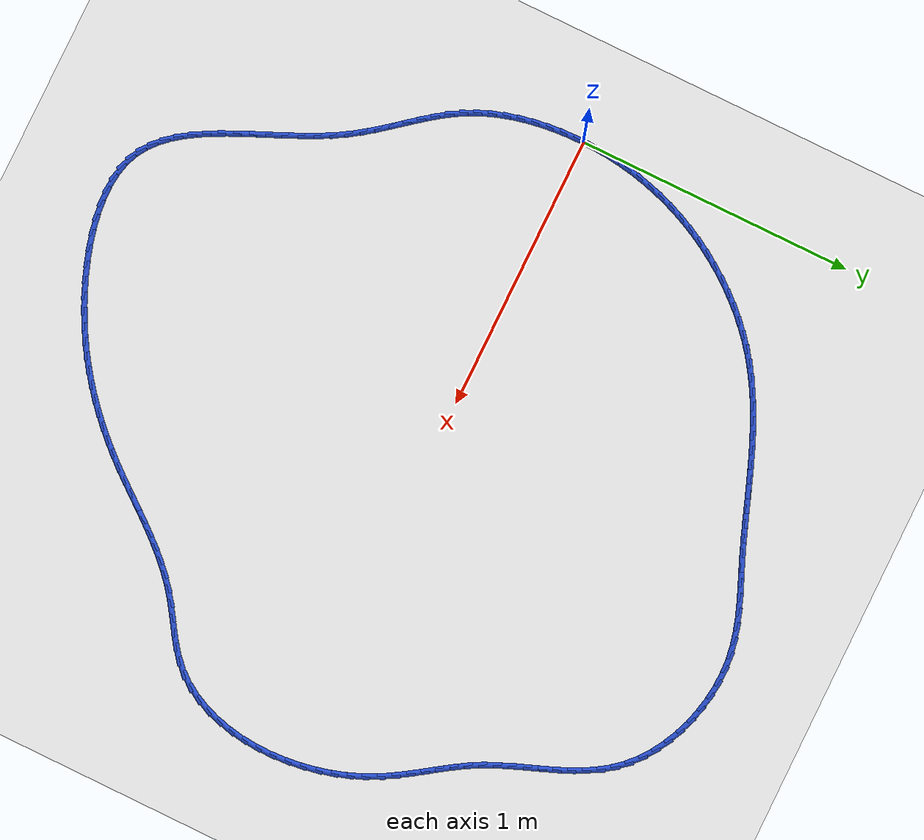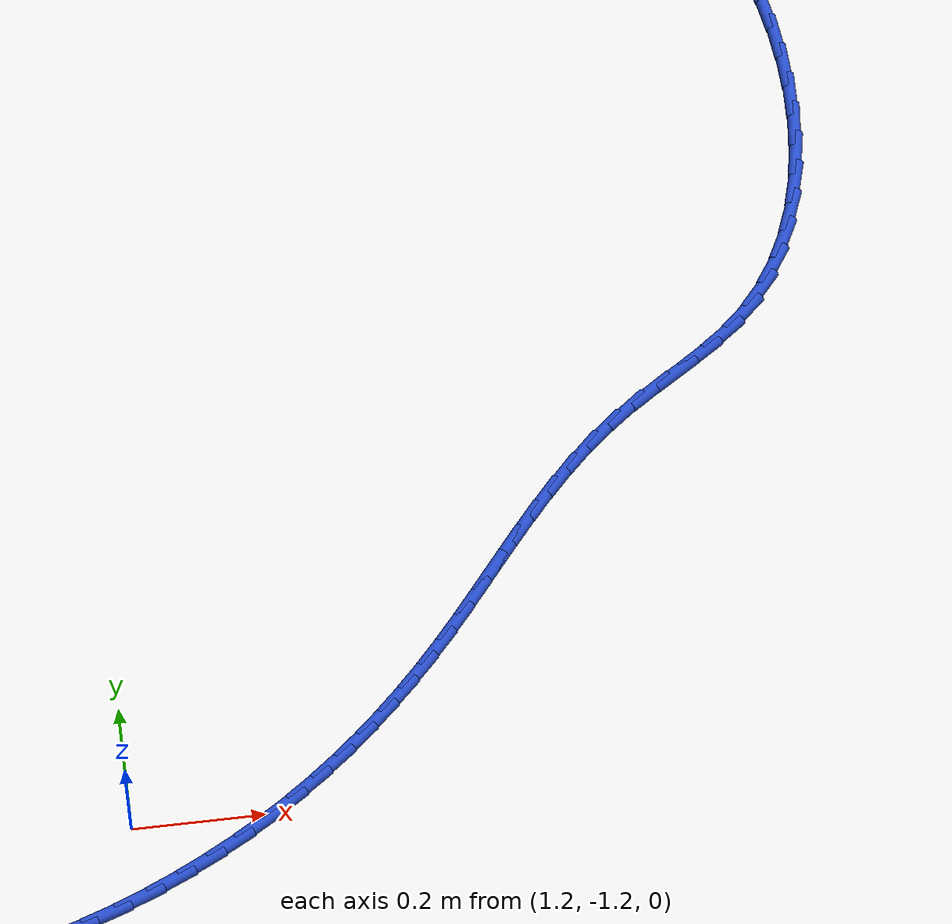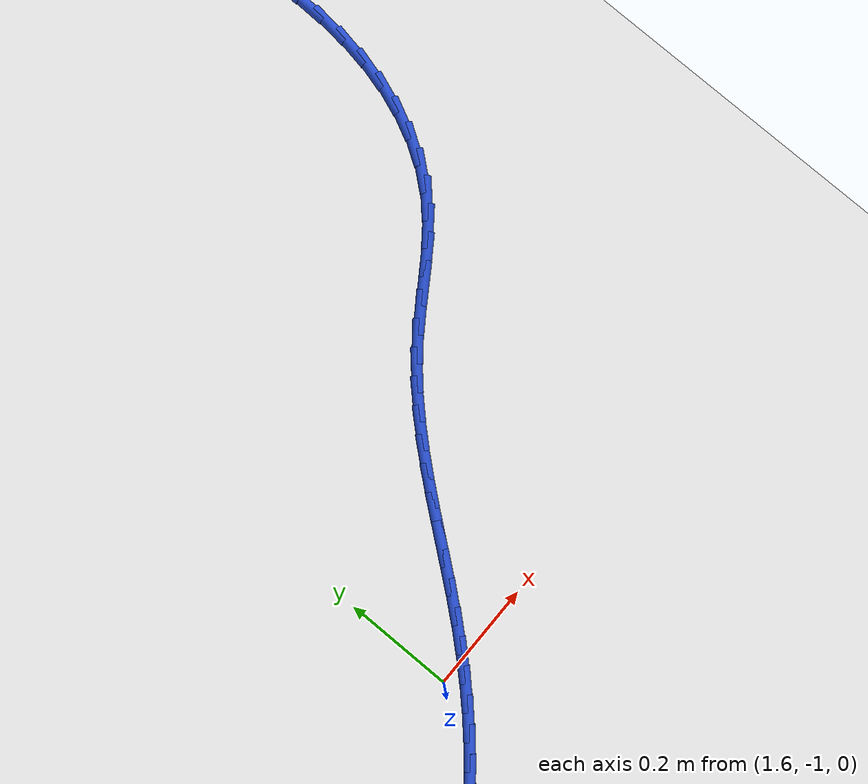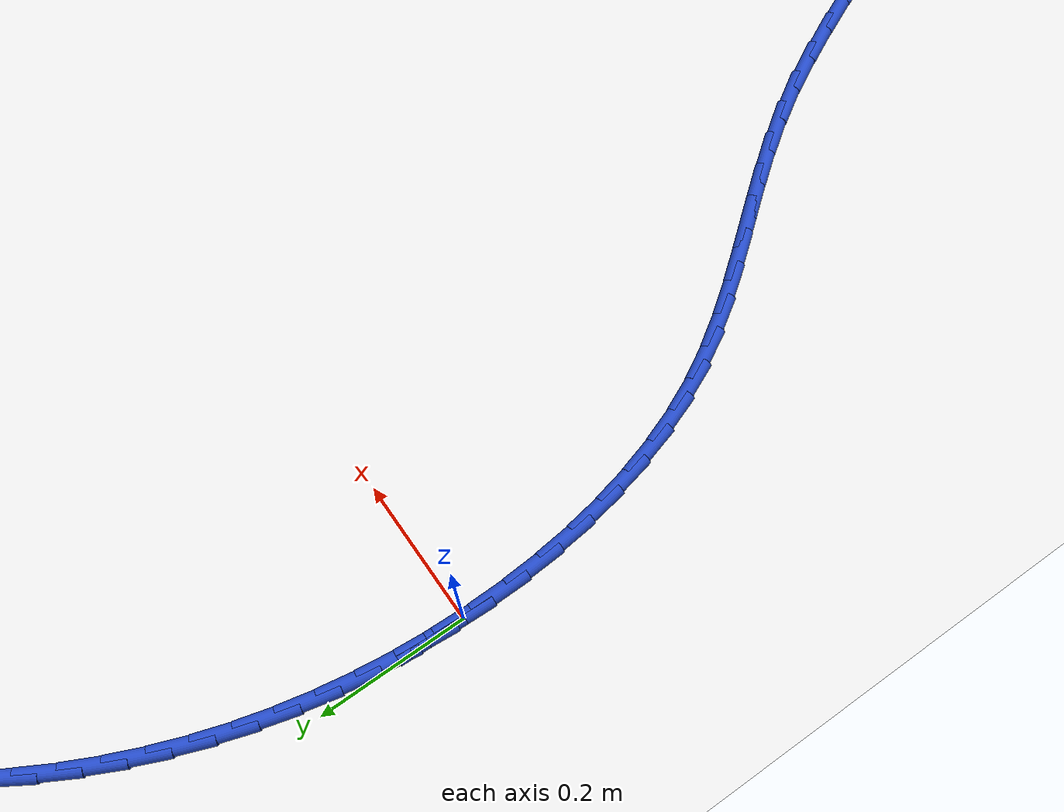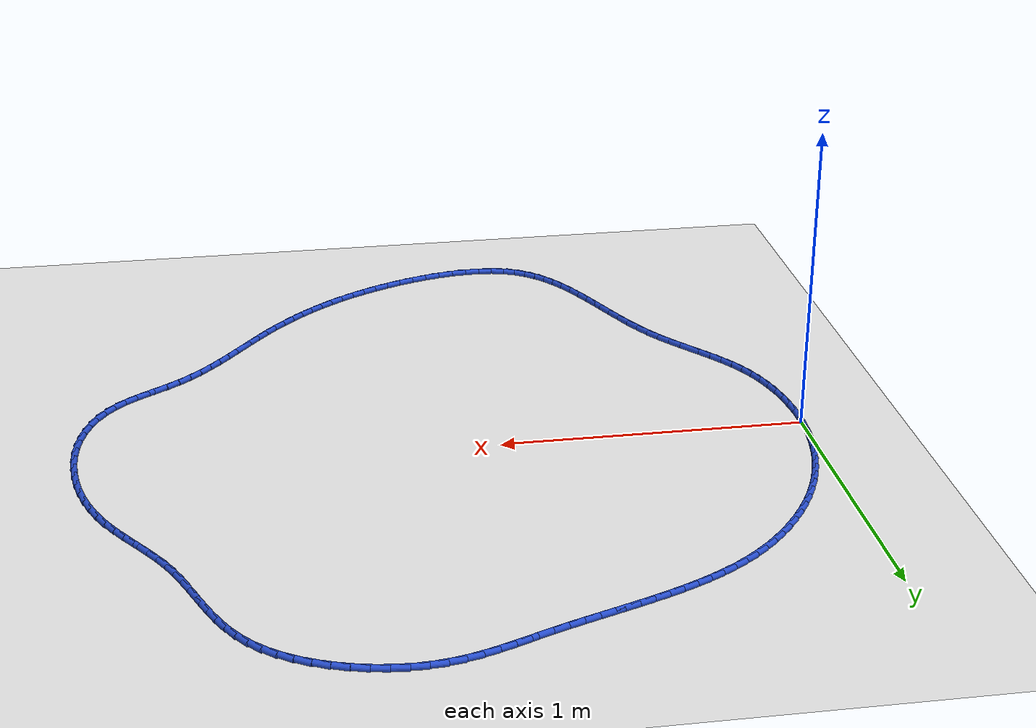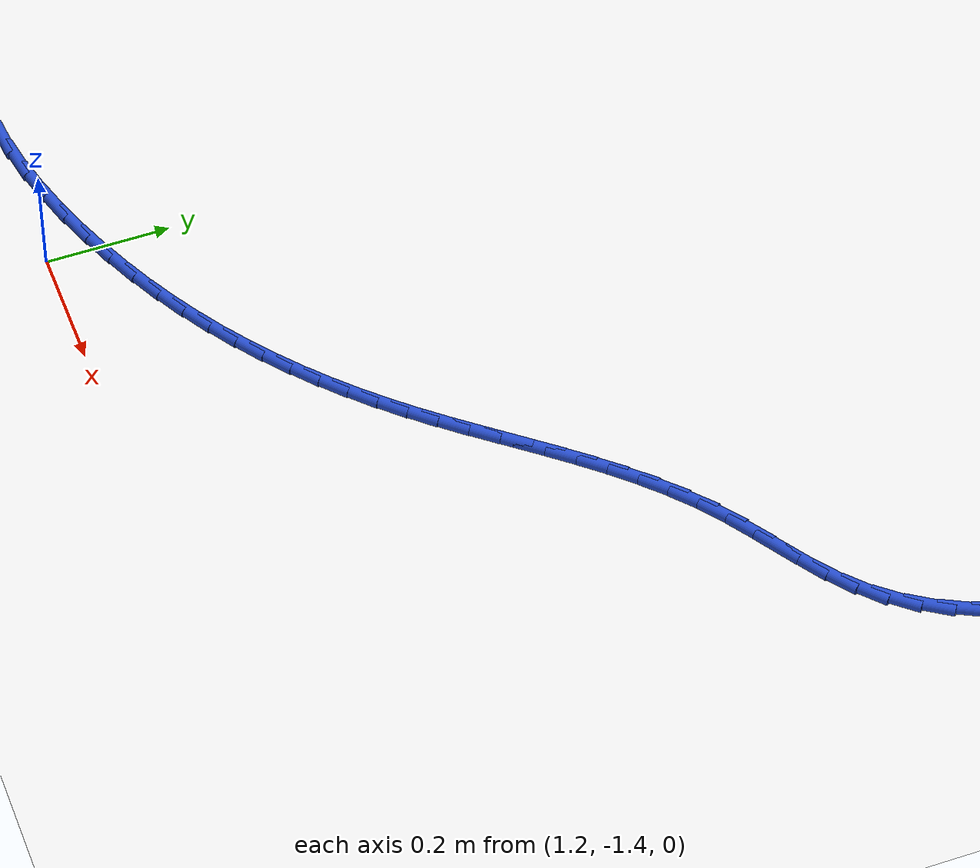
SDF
<sdf version="1.6">
 <world name="default">
  <light name="sun" type="directional">
   <pose>0 0 10 0 -0 0</pose>
   <diffuse>0.8 0.8 0.8 1</diffuse>
   <specular>0.2 0.2 0.2 1</specular>
   <attenuation>
    <range>1000</range>
    <constant>0.9</constant>
    <linear>0.01</linear>
    <quadratic>0.001</quadratic>
   </attenuation>
   <direction>-0.5 0.1 -0.9</direction>
  </light>
  <model name="ground_plane">
   <static>1</static>
   <link name="link">
    <collision name="collision">
     <geometry><plane><normal>0 0 1</normal><size>100 100</size></plane></geometry>
     <surface><friction><ode><mu>100</mu><mu2>50</mu2></ode></friction></surface>
    </collision>
    <visual name="visual">
     <cast_shadows>0</cast_shadows>
     <geometry><plane><normal>0 0 1</normal><size>100 100</size></plane></geometry>
     <material>
      <script><uri>file://media/materials/scripts/gazebo.material</uri><name>Gazebo/WhiteGlow</name></script>
     </material>
    </visual>
   </link>
  </model>
  <gravity>0 0 -9.8</gravity>
  <magnetic_field>6e-06 2.3e-05 -4.2e-05</magnetic_field>
  <atmosphere type="adiabatic"/>
  <physics name="default_physics" default="0" type="ode">
   <max_step_size>0.001</max_step_size>
   <real_time_factor>1</real_time_factor>
   <real_time_update_rate>1000</real_time_update_rate>
  </physics>
  <scene><ambient>0.4 0.4 0.4 1</ambient><background>0.7 0.7 0.7 1</background><shadows>1</shadows></scene>
  <spherical_coordinates>
   <surface_model>EARTH_WGS84</surface_model>
   <latitude_deg>0</latitude_deg>
   <longitude_deg>0</longitude_deg>
   <elevation>0</elevation>
   <heading_deg>0</heading_deg>
  </spherical_coordinates>
  <model name="line">
   <link name="link_0">
    <pose>-2.7755575615628914e-17 4.163336342344337e-17 0.01 0 1.57 1.5334513663498914</pose>
    <collision name="collision">
     <geometry><cylinder><radius>0.01</radius><length>0.08</length></cylinder></geometry>
    </collision>
    <visual name="visual">
     <material>
      <script><name>Gazebo/Blue</name><uri>file://media/materials/scripts/gazebo.material</uri></script>
     </material>
     <geometry><cylinder><radius>0.01</radius><length>0.08</length></cylinder></geometry>
    </visual>
   </link>
   <link name="link_1">
    <pose>0.0019006311215718386 0.05087024989531458 0.01 0 1.57 1.4872357537538161</pose>
    <collision name="collision">
     <geometry><cylinder><radius>0.01</radius><length>0.08</length></cylinder></geometry>
    </collision>
    <visual name="visual">
     <material>
      <script><name>Gazebo/Blue</name><uri>file://media/materials/scripts/gazebo.material</uri></script>
     </material>
     <geometry><cylinder><radius>0.01</radius><length>0.08</length></cylinder></geometry>
    </visual>
   </link>
   <link name="link_2">
    <pose>0.00612523995798891 0.10130996697580699 0.01 0 1.57 1.4404470728081094</pose>
    <collision name="collision">
     <geometry><cylinder><radius>0.01</radius><length>0.08</length></cylinder></geometry>
    </collision>
    <visual name="visual">
     <material>
      <script><name>Gazebo/Blue</name><uri>file://media/materials/scripts/gazebo.material</uri></script>
     </material>
     <geometry><cylinder><radius>0.01</radius><length>0.08</length></cylinder></geometry>
    </visual>
   </link>
   <link name="link_3">
    <pose>0.012675125376173761 0.15127379047608064 0.01 0 1.57 1.3931579620040697</pose>
    <collision name="collision">
     <geometry><cylinder><radius>0.01</radius><length>0.08</length></cylinder></geometry>
    </collision>
    <visual name="visual">
     <material>
      <script><name>Gazebo/Blue</name><uri>file://media/materials/scripts/gazebo.material</uri></script>
     </material>
     <geometry><cylinder><radius>0.01</radius><length>0.08</length></cylinder></geometry>
    </visual>
   </link>
   <link name="link_4">
    <pose>0.021551586243048957 0.20071635963073908 0.01 0 1.57 1.3454496513613934</pose>
    <collision name="collision">
     <geometry><cylinder><radius>0.01</radius><length>0.08</length></cylinder></geometry>
    </collision>
    <visual name="visual">
     <material>
      <script><name>Gazebo/Blue</name><uri>file://media/materials/scripts/gazebo.material</uri></script>
     </material>
     <geometry><cylinder><radius>0.01</radius><length>0.08</length></cylinder></geometry>
    </visual>
   </link>
   <link name="link_5">
    <pose>0.03275592142553706 0.24959231367438556 0.01 0 1.57 1.2974111931169683</pose>
    <collision name="collision">
     <geometry><cylinder><radius>0.01</radius><length>0.08</length></cylinder></geometry>
    </collision>
    <visual name="visual">
     <material>
      <script><name>Gazebo/Blue</name><uri>file://media/materials/scripts/gazebo.material</uri></script>
     </material>
     <geometry><cylinder><radius>0.01</radius><length>0.08</length></cylinder></geometry>
    </visual>
   </link>
   <link name="link_6">
    <pose>0.046289429790560645 0.29785629184162354 0.01 0 1.57 1.2491384111693185</pose>
    <collision name="collision">
     <geometry><cylinder><radius>0.01</radius><length>0.08</length></cylinder></geometry>
    </collision>
    <visual name="visual">
     <material>
      <script><name>Gazebo/Blue</name><uri>file://media/materials/scripts/gazebo.material</uri></script>
     </material>
     <geometry><cylinder><radius>0.01</radius><length>0.08</length></cylinder></geometry>
    </visual>
   </link>
   <link name="link_7">
    <pose>0.06215341020504229 0.3454629333670565 0.01 0 1.57 1.2007325910381488</pose>
    <collision name="collision">
     <geometry><cylinder><radius>0.01</radius><length>0.08</length></cylinder></geometry>
    </collision>
    <visual name="visual">
     <material>
      <script><name>Gazebo/Blue</name><uri>file://media/materials/scripts/gazebo.material</uri></script>
     </material>
     <geometry><cylinder><radius>0.01</radius><length>0.08</length></cylinder></geometry>
    </visual>
   </link>
   <link name="link_8">
    <pose>0.08034916153590455 0.39236687748528776 0.01 0 1.57 1.1523396421303143</pose>
    <collision name="collision">
     <geometry><cylinder><radius>0.01</radius><length>0.08</length></cylinder></geometry>
    </collision>
    <visual name="visual">
     <material>
      <script><name>Gazebo/Blue</name><uri>file://media/materials/scripts/gazebo.material</uri></script>
     </material>
     <geometry><cylinder><radius>0.01</radius><length>0.08</length></cylinder></geometry>
    </visual>
   </link>
   <link name="link_9">
    <pose>0.10087317935745899 0.43851702147689847 0.01 0 1.57 1.1044048622155573</pose>
    <collision name="collision">
     <geometry><cylinder><radius>0.01</radius><length>0.08</length></cylinder></geometry>
    </collision>
    <visual name="visual">
     <material>
      <script><name>Gazebo/Blue</name><uri>file://media/materials/scripts/gazebo.material</uri></script>
     </material>
     <geometry><cylinder><radius>0.01</radius><length>0.08</length></cylinder></geometry>
    </visual>
   </link>
   <link name="link_10">
    <pose>0.12367067826876 0.48380096029800346 0.01 0 1.57 1.0569618173375206</pose>
    <collision name="collision">
     <geometry><cylinder><radius>0.01</radius><length>0.08</length></cylinder></geometry>
    </collision>
    <visual name="visual">
     <material>
      <script><name>Gazebo/Blue</name><uri>file://media/materials/scripts/gazebo.material</uri></script>
     </material>
     <geometry><cylinder><radius>0.01</radius><length>0.08</length></cylinder></geometry>
    </visual>
   </link>
   <link name="link_11">
    <pose>0.14865583118807907 0.52806918104595 0.01 0 1.57 1.0097399459500789</pose>
    <collision name="collision">
     <geometry><cylinder><radius>0.01</radius><length>0.08</length></cylinder></geometry>
    </collision>
    <visual name="visual">
     <material>
      <script><name>Gazebo/Blue</name><uri>file://media/materials/scripts/gazebo.material</uri></script>
     </material>
     <geometry><cylinder><radius>0.01</radius><length>0.08</length></cylinder></geometry>
    </visual>
   </link>
   <link name="link_12">
    <pose>0.17574237816608468 0.5711716533593172 0.01 0 1.57 0.9624675502229438</pose>
    <collision name="collision">
     <geometry><cylinder><radius>0.01</radius><length>0.08</length></cylinder></geometry>
    </collision>
    <visual name="visual">
     <material>
      <script><name>Gazebo/Blue</name><uri>file://media/materials/scripts/gazebo.material</uri></script>
     </material>
     <geometry><cylinder><radius>0.01</radius><length>0.08</length></cylinder></geometry>
    </visual>
   </link>
   <link name="link_13">
    <pose>0.20484405925344518 0.6129583468766846 0.01 0 1.57 0.9148749608358802</pose>
    <collision name="collision">
     <geometry><cylinder><radius>0.01</radius><length>0.08</length></cylinder></geometry>
    </collision>
    <visual name="visual">
     <material>
      <script><name>Gazebo/Blue</name><uri>file://media/materials/scripts/gazebo.material</uri></script>
     </material>
     <geometry><cylinder><radius>0.01</radius><length>0.08</length></cylinder></geometry>
    </visual>
   </link>
   <link name="link_14">
    <pose>0.23587461450082903 0.6532792312366317 0.01 0 1.57 0.8666941565900934</pose>
    <collision name="collision">
     <geometry><cylinder><radius>0.01</radius><length>0.08</length></cylinder></geometry>
    </collision>
    <visual name="visual">
     <material>
      <script><name>Gazebo/Blue</name><uri>file://media/materials/scripts/gazebo.material</uri></script>
     </material>
     <geometry><cylinder><radius>0.01</radius><length>0.08</length></cylinder></geometry>
    </visual>
   </link>
   <link name="link_15">
    <pose>0.26874778395890475 0.6919842760777378 0.01 0 1.57 0.8176587741697361</pose>
    <collision name="collision">
     <geometry><cylinder><radius>0.01</radius><length>0.08</length></cylinder></geometry>
    </collision>
    <visual name="visual">
     <material>
      <script><name>Gazebo/Blue</name><uri>file://media/materials/scripts/gazebo.material</uri></script>
     </material>
     <geometry><cylinder><radius>0.01</radius><length>0.08</length></cylinder></geometry>
    </visual>
   </link>
   <link name="link_16">
    <pose>0.3033773076783406 0.7289234510385822 0.01 0 1.57 0.7675047908296786</pose>
    <collision name="collision">
     <geometry><cylinder><radius>0.01</radius><length>0.08</length></cylinder></geometry>
    </collision>
    <visual name="visual">
     <material>
      <script><name>Gazebo/Blue</name><uri>file://media/materials/scripts/gazebo.material</uri></script>
     </material>
     <geometry><cylinder><radius>0.01</radius><length>0.08</length></cylinder></geometry>
    </visual>
   </link>
   <link name="link_17">
    <pose>0.33967692570980523 0.7639467257577449 0.01 0 1.57 0.7159721910976955</pose>
    <collision name="collision">
     <geometry><cylinder><radius>0.01</radius><length>0.08</length></cylinder></geometry>
    </collision>
    <visual name="visual">
     <material>
      <script><name>Gazebo/Blue</name><uri>file://media/materials/scripts/gazebo.material</uri></script>
     </material>
     <geometry><cylinder><radius>0.01</radius><length>0.08</length></cylinder></geometry>
    </visual>
   </link>
   <link name="link_18">
    <pose>0.377560378103967 0.7969040698738049 0.01 0 1.57 0.662807962164855</pose>
    <collision name="collision">
     <geometry><cylinder><radius>0.01</radius><length>0.08</length></cylinder></geometry>
    </collision>
    <visual name="visual">
     <material>
      <script><name>Gazebo/Blue</name><uri>file://media/materials/scripts/gazebo.material</uri></script>
     </material>
     <geometry><cylinder><radius>0.01</radius><length>0.08</length></cylinder></geometry>
    </visual>
   </link>
   <link name="link_19">
    <pose>0.4169414049114941 0.8276454530253416 0.01 0 1.57 0.6086385172632076</pose>
    <collision name="collision">
     <geometry><cylinder><radius>0.01</radius><length>0.08</length></cylinder></geometry>
    </collision>
    <visual name="visual">
     <material>
      <script><name>Gazebo/Blue</name><uri>file://media/materials/scripts/gazebo.material</uri></script>
     </material>
     <geometry><cylinder><radius>0.01</radius><length>0.08</length></cylinder></geometry>
    </visual>
   </link>
   <link name="link_20">
    <pose>0.45772782872288853 0.8560692767457684 0.01 0 1.57 0.5580137965625362</pose>
    <collision name="collision">
     <geometry><cylinder><radius>0.01</radius><length>0.08</length></cylinder></geometry>
    </collision>
    <visual name="visual">
     <material>
      <script><name>Gazebo/Blue</name><uri>file://media/materials/scripts/gazebo.material</uri></script>
     </material>
     <geometry><cylinder><radius>0.01</radius><length>0.08</length></cylinder></geometry>
    </visual>
   </link>
   <link name="link_21">
    <pose>0.49979644111768334 0.8823279181961199 0.01 0 1.57 0.5127230814076948</pose>
    <collision name="collision">
     <geometry><cylinder><radius>0.01</radius><length>0.08</length></cylinder></geometry>
    </collision>
    <visual name="visual">
     <material>
      <script><name>Gazebo/Blue</name><uri>file://media/materials/scripts/gazebo.material</uri></script>
     </material>
     <geometry><cylinder><radius>0.01</radius><length>0.08</length></cylinder></geometry>
    </visual>
   </link>
   <link name="link_22">
    <pose>0.5430138967645544 0.906656720841677 0.01 0 1.57 0.472970089407893</pose>
    <collision name="collision">
     <geometry><cylinder><radius>0.01</radius><length>0.08</length></cylinder></geometry>
    </collision>
    <visual name="visual">
     <material>
      <script><name>Gazebo/Blue</name><uri>file://media/materials/scripts/gazebo.material</uri></script>
     </material>
     <geometry><cylinder><radius>0.01</radius><length>0.08</length></cylinder></geometry>
    </visual>
   </link>
   <link name="link_23">
    <pose>0.5872468446403787 0.9292910747326818 0.01 0 1.57 0.4388379528739432</pose>
    <collision name="collision">
     <geometry><cylinder><radius>0.01</radius><length>0.08</length></cylinder></geometry>
    </collision>
    <visual name="visual">
     <material>
      <script><name>Gazebo/Blue</name><uri>file://media/materials/scripts/gazebo.material</uri></script>
     </material>
     <geometry><cylinder><radius>0.01</radius><length>0.08</length></cylinder></geometry>
    </visual>
   </link>
   <link name="link_24">
    <pose>0.6323619337220321 0.9504663699193746 0.01 0 1.57 0.4103255392657004</pose>
    <collision name="collision">
     <geometry><cylinder><radius>0.01</radius><length>0.08</length></cylinder></geometry>
    </collision>
    <visual name="visual">
     <material>
      <script><name>Gazebo/Blue</name><uri>file://media/materials/scripts/gazebo.material</uri></script>
     </material>
     <geometry><cylinder><radius>0.01</radius><length>0.08</length></cylinder></geometry>
    </visual>
   </link>
   <link name="link_25">
    <pose>0.6782258129863914 0.9704179964519971 0.01 0 1.57 0.38737990083896984</pose>
    <collision name="collision">
     <geometry><cylinder><radius>0.01</radius><length>0.08</length></cylinder></geometry>
    </collision>
    <visual name="visual">
     <material>
      <script><name>Gazebo/Blue</name><uri>file://media/materials/scripts/gazebo.material</uri></script>
     </material>
     <geometry><cylinder><radius>0.01</radius><length>0.08</length></cylinder></geometry>
    </visual>
   </link>
   <link name="link_26">
    <pose>0.7247051314103325 0.9893813443807903 0.01 0 1.57 0.36992336359389655</pose>
    <collision name="collision">
     <geometry><cylinder><radius>0.01</radius><length>0.08</length></cylinder></geometry>
    </collision>
    <visual name="visual">
     <material>
      <script><name>Gazebo/Blue</name><uri>file://media/materials/scripts/gazebo.material</uri></script>
     </material>
     <geometry><cylinder><radius>0.01</radius><length>0.08</length></cylinder></geometry>
    </visual>
   </link>
   <link name="link_27">
    <pose>0.7716665379707326 1.0075918037559957 0.01 0 1.57 0.3578745169798947</pose>
    <collision name="collision">
     <geometry><cylinder><radius>0.01</radius><length>0.08</length></cylinder></geometry>
    </collision>
    <visual name="visual">
     <material>
      <script><name>Gazebo/Blue</name><uri>file://media/materials/scripts/gazebo.material</uri></script>
     </material>
     <geometry><cylinder><radius>0.01</radius><length>0.08</length></cylinder></geometry>
    </visual>
   </link>
   <link name="link_28">
    <pose>0.8189766816444677 1.0252847646278542 0.01 0 1.57 0.35116330078935415</pose>
    <collision name="collision">
     <geometry><cylinder><radius>0.01</radius><length>0.08</length></cylinder></geometry>
    </collision>
    <visual name="visual">
     <material>
      <script><name>Gazebo/Blue</name><uri>file://media/materials/scripts/gazebo.material</uri></script>
     </material>
     <geometry><cylinder><radius>0.01</radius><length>0.08</length></cylinder></geometry>
    </visual>
   </link>
   <link name="link_29">
    <pose>0.866502211408414 1.0426956170466073 0.01 0 1.57 0.3497407829168274</pose>
    <collision name="collision">
     <geometry><cylinder><radius>0.01</radius><length>0.08</length></cylinder></geometry>
    </collision>
    <visual name="visual">
     <material>
      <script><name>Gazebo/Blue</name><uri>file://media/materials/scripts/gazebo.material</uri></script>
     </material>
     <geometry><cylinder><radius>0.01</radius><length>0.08</length></cylinder></geometry>
    </visual>
   </link>
   <link name="link_30">
    <pose>0.9141097762394482 1.0600597510624958 0.01 0 1.57 0.353584252421457</pose>
    <collision name="collision">
     <geometry><cylinder><radius>0.01</radius><length>0.08</length></cylinder></geometry>
    </collision>
    <visual name="visual">
     <material>
      <script><name>Gazebo/Blue</name><uri>file://media/materials/scripts/gazebo.material</uri></script>
     </material>
     <geometry><cylinder><radius>0.01</radius><length>0.08</length></cylinder></geometry>
    </visual>
   </link>
   <link name="link_31">
    <pose>0.9616660251144468 1.0776125567257615 0.01 0 1.57 0.3626980707452565</pose>
    <collision name="collision">
     <geometry><cylinder><radius>0.01</radius><length>0.08</length></cylinder></geometry>
    </collision>
    <visual name="visual">
     <material>
      <script><name>Gazebo/Blue</name><uri>file://media/materials/scripts/gazebo.material</uri></script>
     </material>
     <geometry><cylinder><radius>0.01</radius><length>0.08</length></cylinder></geometry>
    </visual>
   </link>
   <link name="link_32">
    <pose>1.0090376070102858 1.095589424086645 0.01 0 1.57 0.3771104457581654</pose>
    <collision name="collision">
     <geometry><cylinder><radius>0.01</radius><length>0.08</length></cylinder></geometry>
    </collision>
    <visual name="visual">
     <material>
      <script><name>Gazebo/Blue</name><uri>file://media/materials/scripts/gazebo.material</uri></script>
     </material>
     <geometry><cylinder><radius>0.01</radius><length>0.08</length></cylinder></geometry>
    </visual>
   </link>
   <link name="link_33">
    <pose>1.0560911709038419 1.114225743195388 0.01 0 1.57 0.39311466043362875</pose>
    <collision name="collision">
     <geometry><cylinder><radius>0.01</radius><length>0.08</length></cylinder></geometry>
    </collision>
    <visual name="visual">
     <material>
      <script><name>Gazebo/Blue</name><uri>file://media/materials/scripts/gazebo.material</uri></script>
     </material>
     <geometry><cylinder><radius>0.01</radius><length>0.08</length></cylinder></geometry>
    </visual>
   </link>
   <link name="link_34">
    <pose>1.102762505744604 1.1335803703496343 0.01 0 1.57 0.3952872805518839</pose>
    <collision name="collision">
     <geometry><cylinder><radius>0.01</radius><length>0.08</length></cylinder></geometry>
    </collision>
    <visual name="visual">
     <material>
      <script><name>Gazebo/Blue</name><uri>file://media/materials/scripts/gazebo.material</uri></script>
     </material>
     <geometry><cylinder><radius>0.01</radius><length>0.08</length></cylinder></geometry>
    </visual>
   </link>
   <link name="link_35">
    <pose>1.1492716919898036 1.15298628584799 0.01 0 1.57 0.37953694766471235</pose>
    <collision name="collision">
     <geometry><cylinder><radius>0.01</radius><length>0.08</length></cylinder></geometry>
    </collision>
    <visual name="visual">
     <material>
      <script><name>Gazebo/Blue</name><uri>file://media/materials/scripts/gazebo.material</uri></script>
     </material>
     <geometry><cylinder><radius>0.01</radius><length>0.08</length></cylinder></geometry>
    </visual>
   </link>
   <link name="link_36">
    <pose>1.1959118696095608 1.171589928550213 0.01 0 1.57 0.3456431820549411</pose>
    <collision name="collision">
     <geometry><cylinder><radius>0.01</radius><length>0.08</length></cylinder></geometry>
    </collision>
    <visual name="visual">
     <material>
      <script><name>Gazebo/Blue</name><uri>file://media/materials/scripts/gazebo.material</uri></script>
     </material>
     <geometry><cylinder><radius>0.01</radius><length>0.08</length></cylinder></geometry>
    </visual>
   </link>
   <link name="link_37">
    <pose>1.2429761786291746 1.1885377371751737 0.01 0 1.57 0.2934512831283303</pose>
    <collision name="collision">
     <geometry><cylinder><radius>0.01</radius><length>0.08</length></cylinder></geometry>
    </collision>
    <visual name="visual">
     <material>
      <script><name>Gazebo/Blue</name><uri>file://media/materials/scripts/gazebo.material</uri></script>
     </material>
     <geometry><cylinder><radius>0.01</radius><length>0.08</length></cylinder></geometry>
    </visual>
   </link>
   <link name="link_38">
    <pose>1.2907577590739432 1.2029761504417427 0.01 0 1.57 0.22321090891839387</pose>
    <collision name="collision">
     <geometry><cylinder><radius>0.01</radius><length>0.08</length></cylinder></geometry>
    </collision>
    <visual name="visual">
     <material>
      <script><name>Gazebo/Blue</name><uri>file://media/materials/scripts/gazebo.material</uri></script>
     </material>
     <geometry><cylinder><radius>0.01</radius><length>0.08</length></cylinder></geometry>
    </visual>
   </link>
   <link name="link_39">
    <pose>1.339549750969166 1.2140516070687903 0.01 0 1.57 0.13618608619672748</pose>
    <collision name="collision">
     <geometry><cylinder><radius>0.01</radius><length>0.08</length></cylinder></geometry>
    </collision>
    <visual name="visual">
     <material>
      <script><name>Gazebo/Blue</name><uri>file://media/materials/scripts/gazebo.material</uri></script>
     </material>
     <geometry><cylinder><radius>0.01</radius><length>0.08</length></cylinder></geometry>
    </visual>
   </link>
   <link name="link_40">
    <pose>1.389640515573445 1.2209157605009378 0.01 0 1.57 0.04198628796460396</pose>
    <collision name="collision">
     <geometry><cylinder><radius>0.01</radius><length>0.08</length></cylinder></geometry>
    </collision>
    <visual name="visual">
     <material>
      <script><name>Gazebo/Blue</name><uri>file://media/materials/scripts/gazebo.material</uri></script>
     </material>
     <geometry><cylinder><radius>0.01</radius><length>0.08</length></cylinder></geometry>
    </visual>
   </link>
   <link name="link_41">
    <pose>1.4409949737881937 1.2230732114738059 0.01 0 1.57 -0.047471777325768155</pose>
    <collision name="collision">
     <geometry><cylinder><radius>0.01</radius><length>0.08</length></cylinder></geometry>
    </collision>
    <visual name="visual">
     <material>
      <script><name>Gazebo/Blue</name><uri>file://media/materials/scripts/gazebo.material</uri></script>
     </material>
     <geometry><cylinder><radius>0.01</radius><length>0.08</length></cylinder></geometry>
    </visual>
   </link>
   <link name="link_42">
    <pose>1.4930543796852804 1.2206000008193512 0.01 0 1.57 -0.13295337003043484</pose>
    <collision name="collision">
     <geometry><cylinder><radius>0.01</radius><length>0.08</length></cylinder></geometry>
    </collision>
    <visual name="visual">
     <material>
      <script><name>Gazebo/Blue</name><uri>file://media/materials/scripts/gazebo.material</uri></script>
     </material>
     <geometry><cylinder><radius>0.01</radius><length>0.08</length></cylinder></geometry>
    </visual>
   </link>
   <link name="link_43">
    <pose>1.5452122252929636 1.21362428866612 0.01 0 1.57 -0.2163121100112164</pose>
    <collision name="collision">
     <geometry><cylinder><radius>0.01</radius><length>0.08</length></cylinder></geometry>
    </collision>
    <visual name="visual">
     <material>
      <script><name>Gazebo/Blue</name><uri>file://media/materials/scripts/gazebo.material</uri></script>
     </material>
     <geometry><cylinder><radius>0.01</radius><length>0.08</length></cylinder></geometry>
    </visual>
   </link>
   <link name="link_44">
    <pose>1.5968620026395017 1.2022742351426583 0.01 0 1.57 -0.29934727198102073</pose>
    <collision name="collision">
     <geometry><cylinder><radius>0.01</radius><length>0.08</length></cylinder></geometry>
    </collision>
    <visual name="visual">
     <material>
      <script><name>Gazebo/Blue</name><uri>file://media/materials/scripts/gazebo.material</uri></script>
     </material>
     <geometry><cylinder><radius>0.01</radius><length>0.08</length></cylinder></geometry>
    </visual>
   </link>
   <link name="link_45">
    <pose>1.6473972037531537 1.1866780003775124 0.01 0 1.57 -0.3838328148589107</pose>
    <collision name="collision">
     <geometry><cylinder><radius>0.01</radius><length>0.08</length></cylinder></geometry>
    </collision>
    <visual name="visual">
     <material>
      <script><name>Gazebo/Blue</name><uri>file://media/materials/scripts/gazebo.material</uri></script>
     </material>
     <geometry><cylinder><radius>0.01</radius><length>0.08</length></cylinder></geometry>
    </visual>
   </link>
   <link name="link_46">
    <pose>1.6962113206621763 1.1669637444992278 0.01 0 1.57 -0.47154709653462734</pose>
    <collision name="collision">
     <geometry><cylinder><radius>0.01</radius><length>0.08</length></cylinder></geometry>
    </collision>
    <visual name="visual">
     <material>
      <script><name>Gazebo/Blue</name><uri>file://media/materials/scripts/gazebo.material</uri></script>
     </material>
     <geometry><cylinder><radius>0.01</radius><length>0.08</length></cylinder></geometry>
    </visual>
   </link>
   <link name="link_47">
    <pose>1.7426978453948279 1.1432596276363507 0.01 0 1.57 -0.5642844519139303</pose>
    <collision name="collision">
     <geometry><cylinder><radius>0.01</radius><length>0.08</length></cylinder></geometry>
    </collision>
    <visual name="visual">
     <material>
      <script><name>Gazebo/Blue</name><uri>file://media/materials/scripts/gazebo.material</uri></script>
     </material>
     <geometry><cylinder><radius>0.01</radius><length>0.08</length></cylinder></geometry>
    </visual>
   </link>
   <link name="link_48">
    <pose>1.7862502699793672 1.1156938099174278 0.01 0 1.57 -0.6638254572470048</pose>
    <collision name="collision">
     <geometry><cylinder><radius>0.01</radius><length>0.08</length></cylinder></geometry>
    </collision>
    <visual name="visual">
     <material>
      <script><name>Gazebo/Blue</name><uri>file://media/materials/scripts/gazebo.material</uri></script>
     </material>
     <geometry><cylinder><radius>0.01</radius><length>0.08</length></cylinder></geometry>
    </visual>
   </link>
   <link name="link_49">
    <pose>1.8262620864440522 1.0843944514710042 0.01 0 1.57 -0.7718343643236865</pose>
    <collision name="collision">
     <geometry><cylinder><radius>0.01</radius><length>0.08</length></cylinder></geometry>
    </collision>
    <visual name="visual">
     <material>
      <script><name>Gazebo/Blue</name><uri>file://media/materials/scripts/gazebo.material</uri></script>
     </material>
     <geometry><cylinder><radius>0.01</radius><length>0.08</length></cylinder></geometry>
    </visual>
   </link>
   <link name="link_50">
    <pose>1.8621267868171416 1.0494897124256266 0.01 0 1.57 -0.8867132381240912</pose>
    <collision name="collision">
     <geometry><cylinder><radius>0.01</radius><length>0.08</length></cylinder></geometry>
    </collision>
    <visual name="visual">
     <material>
      <script><name>Gazebo/Blue</name><uri>file://media/materials/scripts/gazebo.material</uri></script>
     </material>
     <geometry><cylinder><radius>0.01</radius><length>0.08</length></cylinder></geometry>
    </visual>
   </link>
   <link name="link_51">
    <pose>1.893386625401366 1.0111546345942737 0.01 0 1.57 -0.9900694901103938</pose>
    <collision name="collision">
     <geometry><cylinder><radius>0.01</radius><length>0.08</length></cylinder></geometry>
    </collision>
    <visual name="visual">
     <material>
      <script><name>Gazebo/Blue</name><uri>file://media/materials/scripts/gazebo.material</uri></script>
     </material>
     <geometry><cylinder><radius>0.01</radius><length>0.08</length></cylinder></geometry>
    </visual>
   </link>
   <link name="link_52">
    <pose>1.920490962531503 0.969850129704805 0.01 0 1.57 -1.0732001886889313</pose>
    <collision name="collision">
     <geometry><cylinder><radius>0.01</radius><length>0.08</length></cylinder></geometry>
    </collision>
    <visual name="visual">
     <material>
      <script><name>Gazebo/Blue</name><uri>file://media/materials/scripts/gazebo.material</uri></script>
     </material>
     <geometry><cylinder><radius>0.01</radius><length>0.08</length></cylinder></geometry>
    </visual>
   </link>
   <link name="link_53">
    <pose>1.9442310286467575 0.9261448481332657 0.01 0 1.57 -1.135667791047885</pose>
    <collision name="collision">
     <geometry><cylinder><radius>0.01</radius><length>0.08</length></cylinder></geometry>
    </collision>
    <visual name="visual">
     <material>
      <script><name>Gazebo/Blue</name><uri>file://media/materials/scripts/gazebo.material</uri></script>
     </material>
     <geometry><cylinder><radius>0.01</radius><length>0.08</length></cylinder></geometry>
    </visual>
   </link>
   <link name="link_54">
    <pose>1.9653986799708347 0.8806076374685458 0.01 0 1.57 -1.178064835925117</pose>
    <collision name="collision">
     <geometry><cylinder><radius>0.01</radius><length>0.08</length></cylinder></geometry>
    </collision>
    <visual name="visual">
     <material>
      <script><name>Gazebo/Blue</name><uri>file://media/materials/scripts/gazebo.material</uri></script>
     </material>
     <geometry><cylinder><radius>0.01</radius><length>0.08</length></cylinder></geometry>
    </visual>
   </link>
   <link name="link_55">
    <pose>1.9847857727274387 0.8338073452995366 0.01 0 1.57 -1.2012170917325466</pose>
    <collision name="collision">
     <geometry><cylinder><radius>0.01</radius><length>0.08</length></cylinder></geometry>
    </collision>
    <visual name="visual">
     <material>
      <script><name>Gazebo/Blue</name><uri>file://media/materials/scripts/gazebo.material</uri></script>
     </material>
     <geometry><cylinder><radius>0.01</radius><length>0.08</length></cylinder></geometry>
    </visual>
   </link>
   <link name="link_56">
    <pose>2.003184163140274 0.7863128192151276 0.01 0 1.57 -1.2057060780142181</pose>
    <collision name="collision">
     <geometry><cylinder><radius>0.01</radius><length>0.08</length></cylinder></geometry>
    </collision>
    <visual name="visual">
     <material>
      <script><name>Gazebo/Blue</name><uri>file://media/materials/scripts/gazebo.material</uri></script>
     </material>
     <geometry><cylinder><radius>0.01</radius><length>0.08</length></cylinder></geometry>
    </visual>
   </link>
   <link name="link_57">
    <pose>2.0213857074330446 0.7386929068042096 0.01 0 1.57 -1.1916433808760836</pose>
    <collision name="collision">
     <geometry><cylinder><radius>0.01</radius><length>0.08</length></cylinder></geometry>
    </collision>
    <visual name="visual">
     <material>
      <script><name>Gazebo/Blue</name><uri>file://media/materials/scripts/gazebo.material</uri></script>
     </material>
     <geometry><cylinder><radius>0.01</radius><length>0.08</length></cylinder></geometry>
    </visual>
   </link>
   <link name="link_58">
    <pose>2.040182261829454 0.691516455655672 0.01 0 1.57 -1.1586293924227349</pose>
    <collision name="collision">
     <geometry><cylinder><radius>0.01</radius><length>0.08</length></cylinder></geometry>
    </collision>
    <visual name="visual">
     <material>
      <script><name>Gazebo/Blue</name><uri>file://media/materials/scripts/gazebo.material</uri></script>
     </material>
     <geometry><cylinder><radius>0.01</radius><length>0.08</length></cylinder></geometry>
    </visual>
   </link>
   <link name="link_59">
    <pose>2.0603656825532077 0.6453523133584061 0.01 0 1.57 -1.10594872293071</pose>
    <collision name="collision">
     <geometry><cylinder><radius>0.01</radius><length>0.08</length></cylinder></geometry>
    </collision>
    <visual name="visual">
     <material>
      <script><name>Gazebo/Blue</name><uri>file://media/materials/scripts/gazebo.material</uri></script>
     </material>
     <geometry><cylinder><radius>0.01</radius><length>0.08</length></cylinder></geometry>
    </visual>
   </link>
   <link name="link_60">
    <pose>2.082725139466468 0.6007672345606511 0.01 0 1.57 -1.044432624830752</pose>
    <collision name="collision">
     <geometry><cylinder><radius>0.01</radius><length>0.08</length></cylinder></geometry>
    </collision>
    <visual name="visual">
     <material>
      <script><name>Gazebo/Blue</name><uri>file://media/materials/scripts/gazebo.material</uri></script>
     </material>
     <geometry><cylinder><radius>0.01</radius><length>0.08</length></cylinder></geometry>
    </visual>
   </link>
   <link name="link_61">
    <pose>2.1075915912603733 0.5579709822059038 0.01 0 1.57 -0.9991546788799175</pose>
    <collision name="collision">
     <geometry><cylinder><radius>0.01</radius><length>0.08</length></cylinder></geometry>
    </collision>
    <visual name="visual">
     <material>
      <script><name>Gazebo/Blue</name><uri>file://media/materials/scripts/gazebo.material</uri></script>
     </material>
     <geometry><cylinder><radius>0.01</radius><length>0.08</length></cylinder></geometry>
    </visual>
   </link>
   <link name="link_62">
    <pose>2.1343235674775496 0.5164157010008655 0.01 0 1.57 -0.9739570257803845</pose>
    <collision name="collision">
     <geometry><cylinder><radius>0.01</radius><length>0.08</length></cylinder></geometry>
    </collision>
    <visual name="visual">
     <material>
      <script><name>Gazebo/Blue</name><uri>file://media/materials/scripts/gazebo.material</uri></script>
     </material>
     <geometry><cylinder><radius>0.01</radius><length>0.08</length></cylinder></geometry>
    </visual>
   </link>
   <link name="link_63">
    <pose>2.16215542336667 0.47545679162746246 0.01 0 1.57 -0.9689448793260904</pose>
    <collision name="collision">
     <geometry><cylinder><radius>0.01</radius><length>0.08</length></cylinder></geometry>
    </collision>
    <visual name="visual">
     <material>
      <script><name>Gazebo/Blue</name><uri>file://media/materials/scripts/gazebo.material</uri></script>
     </material>
     <geometry><cylinder><radius>0.01</radius><length>0.08</length></cylinder></geometry>
    </visual>
   </link>
   <link name="link_64">
    <pose>2.1903215141764116 0.43444965476762065 0.01 0 1.57 -0.9838785386937565</pose>
    <collision name="collision">
     <geometry><cylinder><radius>0.01</radius><length>0.08</length></cylinder></geometry>
    </collision>
    <visual name="visual">
     <material>
      <script><name>Gazebo/Blue</name><uri>file://media/materials/scripts/gazebo.material</uri></script>
     </material>
     <geometry><cylinder><radius>0.01</radius><length>0.08</length></cylinder></geometry>
    </visual>
   </link>
   <link name="link_65">
    <pose>2.2180561951554507 0.39274969110326613 0.01 0 1.57 -1.0182472833251086</pose>
    <collision name="collision">
     <geometry><cylinder><radius>0.01</radius><length>0.08</length></cylinder></geometry>
    </collision>
    <visual name="visual">
     <material>
      <script><name>Gazebo/Blue</name><uri>file://media/materials/scripts/gazebo.material</uri></script>
     </material>
     <geometry><cylinder><radius>0.01</radius><length>0.08</length></cylinder></geometry>
    </visual>
   </link>
   <link name="link_66">
    <pose>2.2445938215524617 0.349712301316325 0.01 0 1.57 -1.0711264088432597</pose>
    <collision name="collision">
     <geometry><cylinder><radius>0.01</radius><length>0.08</length></cylinder></geometry>
    </collision>
    <visual name="visual">
     <material>
      <script><name>Gazebo/Blue</name><uri>file://media/materials/scripts/gazebo.material</uri></script>
     </material>
     <geometry><cylinder><radius>0.01</radius><length>0.08</length></cylinder></geometry>
    </visual>
   </link>
   <link name="link_67">
    <pose>2.2691687486161216 0.3046928860887228 0.01 0 1.57 -1.1397565086121426</pose>
    <collision name="collision">
     <geometry><cylinder><radius>0.01</radius><length>0.08</length></cylinder></geometry>
    </collision>
    <visual name="visual">
     <material>
      <script><name>Gazebo/Blue</name><uri>file://media/materials/scripts/gazebo.material</uri></script>
     </material>
     <geometry><cylinder><radius>0.01</radius><length>0.08</length></cylinder></geometry>
    </visual>
   </link>
   <link name="link_68">
    <pose>2.291051188936686 0.25710996632728134 0.01 0 1.57 -1.2108532033038288</pose>
    <collision name="collision">
     <geometry><cylinder><radius>0.01</radius><length>0.08</length></cylinder></geometry>
    </collision>
    <visual name="visual">
     <material>
      <script><name>Gazebo/Blue</name><uri>file://media/materials/scripts/gazebo.material</uri></script>
     </material>
     <geometry><cylinder><radius>0.01</radius><length>0.08</length></cylinder></geometry>
    </visual>
   </link>
   <link name="link_69">
    <pose>2.3098907099884003 0.20704984712295665 0.01 0 1.57 -1.278293907115685</pose>
    <collision name="collision">
     <geometry><cylinder><radius>0.01</radius><length>0.08</length></cylinder></geometry>
    </collision>
    <visual name="visual">
     <material>
      <script><name>Gazebo/Blue</name><uri>file://media/materials/scripts/gazebo.material</uri></script>
     </material>
     <geometry><cylinder><radius>0.01</radius><length>0.08</length></cylinder></geometry>
    </visual>
   </link>
   <link name="link_70">
    <pose>2.3255649253345454 0.15500026657294702 0.01 0 1.57 -1.343413978573037</pose>
    <collision name="collision">
     <geometry><cylinder><radius>0.01</radius><length>0.08</length></cylinder></geometry>
    </collision>
    <visual name="visual">
     <material>
      <script><name>Gazebo/Blue</name><uri>file://media/materials/scripts/gazebo.material</uri></script>
     </material>
     <geometry><cylinder><radius>0.01</radius><length>0.08</length></cylinder></geometry>
    </visual>
   </link>
   <link name="link_71">
    <pose>2.337954564886143 0.10145444852886909 0.01 0 1.57 -1.4075331948183472</pose>
    <collision name="collision">
     <geometry><cylinder><radius>0.01</radius><length>0.08</length></cylinder></geometry>
    </collision>
    <visual name="visual">
     <material>
      <script><name>Gazebo/Blue</name><uri>file://media/materials/scripts/gazebo.material</uri></script>
     </material>
     <geometry><cylinder><radius>0.01</radius><length>0.08</length></cylinder></geometry>
    </visual>
   </link>
   <link name="link_72">
    <pose>2.3469403585542103 0.04690561684234084 0.01 0 1.57 -1.4719043046339715</pose>
    <collision name="collision">
     <geometry><cylinder><radius>0.01</radius><length>0.08</length></cylinder></geometry>
    </collision>
    <visual name="visual">
     <material>
      <script><name>Gazebo/Blue</name><uri>file://media/materials/scripts/gazebo.material</uri></script>
     </material>
     <geometry><cylinder><radius>0.01</radius><length>0.08</length></cylinder></geometry>
    </visual>
   </link>
   <link name="link_73">
    <pose>2.3524030362497657 -0.00815300463502144 0.01 0 1.57 -1.5377573242510014</pose>
    <collision name="collision">
     <geometry><cylinder><radius>0.01</radius><length>0.08</length></cylinder></geometry>
    </collision>
    <visual name="visual">
     <material>
      <script><name>Gazebo/Blue</name><uri>file://media/materials/scripts/gazebo.material</uri></script>
     </material>
     <geometry><cylinder><radius>0.01</radius><length>0.08</length></cylinder></geometry>
    </visual>
   </link>
   <link name="link_74">
    <pose>2.3542233278838296 -0.06322819205160066 0.01 0 1.57 1.5352542161491665</pose>
    <collision name="collision">
     <geometry><cylinder><radius>0.01</radius><length>0.08</length></cylinder></geometry>
    </collision>
    <visual name="visual">
     <material>
      <script><name>Gazebo/Blue</name><uri>file://media/materials/scripts/gazebo.material</uri></script>
     </material>
     <geometry><cylinder><radius>0.01</radius><length>0.08</length></cylinder></geometry>
    </visual>
   </link>
   <link name="link_75">
    <pose>2.3522819633674206 -0.11782672155578001 0.01 0 1.57 1.462653083772761</pose>
    <collision name="collision">
     <geometry><cylinder><radius>0.01</radius><length>0.08</length></cylinder></geometry>
    </collision>
    <visual name="visual">
     <material>
      <script><name>Gazebo/Blue</name><uri>file://media/materials/scripts/gazebo.material</uri></script>
     </material>
     <geometry><cylinder><radius>0.01</radius><length>0.08</length></cylinder></geometry>
    </visual>
   </link>
   <link name="link_76">
    <pose>2.3464596726115565 -0.17145536929594282 0.01 0 1.57 1.3846809257380137</pose>
    <collision name="collision">
     <geometry><cylinder><radius>0.01</radius><length>0.08</length></cylinder></geometry>
    </collision>
    <visual name="visual">
     <material>
      <script><name>Gazebo/Blue</name><uri>file://media/materials/scripts/gazebo.material</uri></script>
     </material>
     <geometry><cylinder><radius>0.01</radius><length>0.08</length></cylinder></geometry>
    </visual>
   </link>
   <link name="link_77">
    <pose>2.3366371855272585 -0.22362091142047172 0.01 0 1.57 1.2999428534817339</pose>
    <collision name="collision">
     <geometry><cylinder><radius>0.01</radius><length>0.08</length></cylinder></geometry>
    </collision>
    <visual name="visual">
     <material>
      <script><name>Gazebo/Blue</name><uri>file://media/materials/scripts/gazebo.material</uri></script>
     </material>
     <geometry><cylinder><radius>0.01</radius><length>0.08</length></cylinder></geometry>
    </visual>
   </link>
   <link name="link_78">
    <pose>2.3226952320255436 -0.273830124077749 0.01 0 1.57 1.2070636128257792</pose>
    <collision name="collision">
     <geometry><cylinder><radius>0.01</radius><length>0.08</length></cylinder></geometry>
    </collision>
    <visual name="visual">
     <material>
      <script><name>Gazebo/Blue</name><uri>file://media/materials/scripts/gazebo.material</uri></script>
     </material>
     <geometry><cylinder><radius>0.01</radius><length>0.08</length></cylinder></geometry>
    </visual>
   </link>
   <link name="link_79">
    <pose>2.304514542017432 -0.3215897834161593 0.01 0 1.57 1.104826306673661</pose>
    <collision name="collision">
     <geometry><cylinder><radius>0.01</radius><length>0.08</length></cylinder></geometry>
    </collision>
    <visual name="visual">
     <material>
      <script><name>Gazebo/Blue</name><uri>file://media/materials/scripts/gazebo.material</uri></script>
     </material>
     <geometry><cylinder><radius>0.01</radius><length>0.08</length></cylinder></geometry>
    </visual>
   </link>
   <link name="link_80">
    <pose>2.281975845413942 -0.366406665584084 0.01 0 1.57 0.9924123202326143</pose>
    <collision name="collision">
     <geometry><cylinder><radius>0.01</radius><length>0.08</length></cylinder></geometry>
    </collision>
    <visual name="visual">
     <material>
      <script><name>Gazebo/Blue</name><uri>file://media/materials/scripts/gazebo.material</uri></script>
     </material>
     <geometry><cylinder><radius>0.01</radius><length>0.08</length></cylinder></geometry>
    </visual>
   </link>
   <link name="link_81">
    <pose>2.254959872126093 -0.4077875467299079 0.01 0 1.57 0.8697441000128217</pose>
    <collision name="collision">
     <geometry><cylinder><radius>0.01</radius><length>0.08</length></cylinder></geometry>
    </collision>
    <visual name="visual">
     <material>
      <script><name>Gazebo/Blue</name><uri>file://media/materials/scripts/gazebo.material</uri></script>
     </material>
     <geometry><cylinder><radius>0.01</radius><length>0.08</length></cylinder></geometry>
    </visual>
   </link>
   <link name="link_82">
    <pose>2.2233473520649034 -0.44523920300201303 0.01 0 1.57 0.742580368761801</pose>
    <collision name="collision">
     <geometry><cylinder><radius>0.01</radius><length>0.08</length></cylinder></geometry>
    </collision>
    <visual name="visual">
     <material>
      <script><name>Gazebo/Blue</name><uri>file://media/materials/scripts/gazebo.material</uri></script>
     </material>
     <geometry><cylinder><radius>0.01</radius><length>0.08</length></cylinder></geometry>
    </visual>
   </link>
   <link name="link_83">
    <pose>2.187164941681696 -0.47844859245238525 0.01 0 1.57 0.6452162542716688</pose>
    <collision name="collision">
     <geometry><cylinder><radius>0.01</radius><length>0.08</length></cylinder></geometry>
    </collision>
    <visual name="visual">
     <material>
      <script><name>Gazebo/Blue</name><uri>file://media/materials/scripts/gazebo.material</uri></script>
     </material>
     <geometry><cylinder><radius>0.01</radius><length>0.08</length></cylinder></geometry>
    </visual>
   </link>
   <link name="link_84">
    <pose>2.147445339004207 -0.508344876819664 0.01 0 1.57 0.5908001423601669</pose>
    <collision name="collision">
     <geometry><cylinder><radius>0.01</radius><length>0.08</length></cylinder></geometry>
    </collision>
    <visual name="visual">
     <material>
      <script><name>Gazebo/Blue</name><uri>file://media/materials/scripts/gazebo.material</uri></script>
     </material>
     <geometry><cylinder><radius>0.01</radius><length>0.08</length></cylinder></geometry>
    </visual>
   </link>
   <link name="link_85">
    <pose>2.105645286398673 -0.5363808039973027 0.01 0 1.57 0.577297307391716</pose>
    <collision name="collision">
     <geometry><cylinder><radius>0.01</radius><length>0.08</length></cylinder></geometry>
    </collision>
    <visual name="visual">
     <material>
      <script><name>Gazebo/Blue</name><uri>file://media/materials/scripts/gazebo.material</uri></script>
     </material>
     <geometry><cylinder><radius>0.01</radius><length>0.08</length></cylinder></geometry>
    </visual>
   </link>
   <link name="link_86">
    <pose>2.063223013739167 -0.5640109585699677 0.01 0 1.57 0.6037295384172106</pose>
    <collision name="collision">
     <geometry><cylinder><radius>0.01</radius><length>0.08</length></cylinder></geometry>
    </collision>
    <visual name="visual">
     <material>
      <script><name>Gazebo/Blue</name><uri>file://media/materials/scripts/gazebo.material</uri></script>
     </material>
     <geometry><cylinder><radius>0.01</radius><length>0.08</length></cylinder></geometry>
    </visual>
   </link>
   <link name="link_87">
    <pose>2.021636750899761 -0.592689925122324 0.01 0 1.57 0.6657687123250827</pose>
    <collision name="collision">
     <geometry><cylinder><radius>0.01</radius><length>0.08</length></cylinder></geometry>
    </collision>
    <visual name="visual">
     <material>
      <script><name>Gazebo/Blue</name><uri>file://media/materials/scripts/gazebo.material</uri></script>
     </material>
     <geometry><cylinder><radius>0.01</radius><length>0.08</length></cylinder></geometry>
    </visual>
   </link>
   <link name="link_88">
    <pose>1.9821662827363558 -0.6236896368322442 0.01 0 1.57 0.7310450905245823</pose>
    <collision name="collision">
     <geometry><cylinder><radius>0.01</radius><length>0.08</length></cylinder></geometry>
    </collision>
    <visual name="visual">
     <material>
      <script><name>Gazebo/Blue</name><uri>file://media/materials/scripts/gazebo.material</uri></script>
     </material>
     <geometry><cylinder><radius>0.01</radius><length>0.08</length></cylinder></geometry>
    </visual>
   </link>
   <link name="link_89">
    <pose>1.9449247564454646 -0.6570878886949666 0.01 0 1.57 0.7857737313233586</pose>
    <collision name="collision">
     <geometry><cylinder><radius>0.01</radius><length>0.08</length></cylinder></geometry>
    </collision>
    <visual name="visual">
     <material>
      <script><name>Gazebo/Blue</name><uri>file://media/materials/scripts/gazebo.material</uri></script>
     </material>
     <geometry><cylinder><radius>0.01</radius><length>0.08</length></cylinder></geometry>
    </visual>
   </link>
   <link name="link_90">
    <pose>1.9095565574167468 -0.6924826640284464 0.01 0 1.57 0.8296413809363786</pose>
    <collision name="collision">
     <geometry><cylinder><radius>0.01</radius><length>0.08</length></cylinder></geometry>
    </collision>
    <visual name="visual">
     <material>
      <script><name>Gazebo/Blue</name><uri>file://media/materials/scripts/gazebo.material</uri></script>
     </material>
     <geometry><cylinder><radius>0.01</radius><length>0.08</length></cylinder></geometry>
    </visual>
   </link>
   <link name="link_91">
    <pose>1.8757048004314842 -0.7294706455908919 0.01 0 1.57 0.8626487404103224</pose>
    <collision name="collision">
     <geometry><cylinder><radius>0.01</radius><length>0.08</length></cylinder></geometry>
    </collision>
    <visual name="visual">
     <material>
      <script><name>Gazebo/Blue</name><uri>file://media/materials/scripts/gazebo.material</uri></script>
     </material>
     <geometry><cylinder><radius>0.01</radius><length>0.08</length></cylinder></geometry>
    </visual>
   </link>
   <link name="link_92">
    <pose>1.8430126002709573 -0.767648516140514 0.01 0 1.57 0.8849203216156811</pose>
    <collision name="collision">
     <geometry><cylinder><radius>0.01</radius><length>0.08</length></cylinder></geometry>
    </collision>
    <visual name="visual">
     <material>
      <script><name>Gazebo/Blue</name><uri>file://media/materials/scripts/gazebo.material</uri></script>
     </material>
     <geometry><cylinder><radius>0.01</radius><length>0.08</length></cylinder></geometry>
    </visual>
   </link>
   <link name="link_93">
    <pose>1.811123071716449 -0.8066129584355205 0.01 0 1.57 0.8965889323679145</pose>
    <collision name="collision">
     <geometry><cylinder><radius>0.01</radius><length>0.08</length></cylinder></geometry>
    </collision>
    <visual name="visual">
     <material>
      <script><name>Gazebo/Blue</name><uri>file://media/materials/scripts/gazebo.material</uri></script>
     </material>
     <geometry><cylinder><radius>0.01</radius><length>0.08</length></cylinder></geometry>
    </visual>
   </link>
   <link name="link_94">
    <pose>1.7796793295492397 -0.8459606552341223 0.01 0 1.57 0.8977207104698512</pose>
    <collision name="collision">
     <geometry><cylinder><radius>0.01</radius><length>0.08</length></cylinder></geometry>
    </collision>
    <visual name="visual">
     <material>
      <script><name>Gazebo/Blue</name><uri>file://media/materials/scripts/gazebo.material</uri></script>
     </material>
     <geometry><cylinder><radius>0.01</radius><length>0.08</length></cylinder></geometry>
    </visual>
   </link>
   <link name="link_95">
    <pose>1.7483244885506108 -0.8852882892945279 0.01 0 1.57 0.8882766905712431</pose>
    <collision name="collision">
     <geometry><cylinder><radius>0.01</radius><length>0.08</length></cylinder></geometry>
    </collision>
    <visual name="visual">
     <material>
      <script><name>Gazebo/Blue</name><uri>file://media/materials/scripts/gazebo.material</uri></script>
     </material>
     <geometry><cylinder><radius>0.01</radius><length>0.08</length></cylinder></geometry>
    </visual>
   </link>
   <link name="link_96">
    <pose>1.7167016635018457 -0.9241925433749459 0.01 0 1.57 0.8681086555003331</pose>
    <collision name="collision">
     <geometry><cylinder><radius>0.01</radius><length>0.08</length></cylinder></geometry>
    </collision>
    <visual name="visual">
     <material>
      <script><name>Gazebo/Blue</name><uri>file://media/materials/scripts/gazebo.material</uri></script>
     </material>
     <geometry><cylinder><radius>0.01</radius><length>0.08</length></cylinder></geometry>
    </visual>
   </link>
   <link name="link_97">
    <pose>1.6844540009546607 -0.9622701433061315 0.01 0 1.57 0.8389535748512726</pose>
    <collision name="collision">
     <geometry><cylinder><radius>0.01</radius><length>0.08</length></cylinder></geometry>
    </collision>
    <visual name="visual">
     <material>
      <script><name>Gazebo/Blue</name><uri>file://media/materials/scripts/gazebo.material</uri></script>
     </material>
     <geometry><cylinder><radius>0.01</radius><length>0.08</length></cylinder></geometry>
    </visual>
   </link>
   <link name="link_98">
    <pose>1.6512838247755741 -0.9991980441418683 0.01 0 1.57 0.806756025453646</pose>
    <collision name="collision">
     <geometry><cylinder><radius>0.01</radius><length>0.08</length></cylinder></geometry>
    </collision>
    <visual name="visual">
     <material>
      <script><name>Gazebo/Blue</name><uri>file://media/materials/scripts/gazebo.material</uri></script>
     </material>
     <geometry><cylinder><radius>0.01</radius><length>0.08</length></cylinder></geometry>
    </visual>
   </link>
   <link name="link_99">
    <pose>1.6170753842540297 -1.0348998450322717 0.01 0 1.57 0.7727713963493501</pose>
    <collision name="collision">
     <geometry><cylinder><radius>0.01</radius><length>0.08</length></cylinder></geometry>
    </collision>
    <visual name="visual">
     <material>
      <script><name>Gazebo/Blue</name><uri>file://media/materials/scripts/gazebo.material</uri></script>
     </material>
     <geometry><cylinder><radius>0.01</radius><length>0.08</length></cylinder></geometry>
    </visual>
   </link>
   <link name="link_100">
    <pose>1.581747774033884 -1.0693463864685033 0.01 0 1.57 0.7371421829267862</pose>
    <collision name="collision">
     <geometry><cylinder><radius>0.01</radius><length>0.08</length></cylinder></geometry>
    </collision>
    <visual name="visual">
     <material>
      <script><name>Gazebo/Blue</name><uri>file://media/materials/scripts/gazebo.material</uri></script>
     </material>
     <geometry><cylinder><radius>0.01</radius><length>0.08</length></cylinder></geometry>
    </visual>
   </link>
   <link name="link_101">
    <pose>1.5452200887589922 -1.1025085089417235 0.01 0 1.57 0.7000424575247742</pose>
    <collision name="collision">
     <geometry><cylinder><radius>0.01</radius><length>0.08</length></cylinder></geometry>
    </collision>
    <visual name="visual">
     <material>
      <script><name>Gazebo/Blue</name><uri>file://media/materials/scripts/gazebo.material</uri></script>
     </material>
     <geometry><cylinder><radius>0.01</radius><length>0.08</length></cylinder></geometry>
    </visual>
   </link>
   <link name="link_102">
    <pose>1.5074114230732096 -1.1343570529430953 0.01 0 1.57 0.6616762891711171</pose>
    <collision name="collision">
     <geometry><cylinder><radius>0.01</radius><length>0.08</length></cylinder></geometry>
    </collision>
    <visual name="visual">
     <material>
      <script><name>Gazebo/Blue</name><uri>file://media/materials/scripts/gazebo.material</uri></script>
     </material>
     <geometry><cylinder><radius>0.01</radius><length>0.08</length></cylinder></geometry>
    </visual>
   </link>
   <link name="link_103">
    <pose>1.468240871620393 -1.1648628589637806 0.01 0 1.57 0.622274417821732</pose>
    <collision name="collision">
     <geometry><cylinder><radius>0.01</radius><length>0.08</length></cylinder></geometry>
    </collision>
    <visual name="visual">
     <material>
      <script><name>Gazebo/Blue</name><uri>file://media/materials/scripts/gazebo.material</uri></script>
     </material>
     <geometry><cylinder><radius>0.01</radius><length>0.08</length></cylinder></geometry>
    </visual>
   </link>
   <link name="link_104">
    <pose>1.4276275290443972 -1.1939967674949399 0.01 0 1.57 0.582089200319888</pose>
    <collision name="collision">
     <geometry><cylinder><radius>0.01</radius><length>0.08</length></cylinder></geometry>
    </collision>
    <visual name="visual">
     <material>
      <script><name>Gazebo/Blue</name><uri>file://media/materials/scripts/gazebo.material</uri></script>
     </material>
     <geometry><cylinder><radius>0.01</radius><length>0.08</length></cylinder></geometry>
    </visual>
   </link>
   <link name="link_105">
    <pose>1.385490489989078 -1.221729619027736 0.01 0 1.57 0.5413880377799647</pose>
    <collision name="collision">
     <geometry><cylinder><radius>0.01</radius><length>0.08</length></cylinder></geometry>
    </collision>
    <visual name="visual">
     <material>
      <script><name>Gazebo/Blue</name><uri>file://media/materials/scripts/gazebo.material</uri></script>
     </material>
     <geometry><cylinder><radius>0.01</radius><length>0.08</length></cylinder></geometry>
    </visual>
   </link>
   <link name="link_106">
    <pose>1.3417488490982914 -1.24803225405333 0.01 0 1.57 0.5004456832692312</pose>
    <collision name="collision">
     <geometry><cylinder><radius>0.01</radius><length>0.08</length></cylinder></geometry>
    </collision>
    <visual name="visual">
     <material>
      <script><name>Gazebo/Blue</name><uri>file://media/materials/scripts/gazebo.material</uri></script>
     </material>
     <geometry><cylinder><radius>0.01</radius><length>0.08</length></cylinder></geometry>
    </visual>
   </link>
   <link name="link_107">
    <pose>1.296321701015893 -1.2728755130628846 0.01 0 1.57 0.45953597873217544</pose>
    <collision name="collision">
     <geometry><cylinder><radius>0.01</radius><length>0.08</length></cylinder></geometry>
    </collision>
    <visual name="visual">
     <material>
      <script><name>Gazebo/Blue</name><uri>file://media/materials/scripts/gazebo.material</uri></script>
     </material>
     <geometry><cylinder><radius>0.01</radius><length>0.08</length></cylinder></geometry>
    </visual>
   </link>
   <link name="link_108">
    <pose>1.2491281403857377 -1.2962302365475609 0.01 0 1.57 0.41892226512629277</pose>
    <collision name="collision">
     <geometry><cylinder><radius>0.01</radius><length>0.08</length></cylinder></geometry>
    </collision>
    <visual name="visual">
     <material>
      <script><name>Gazebo/Blue</name><uri>file://media/materials/scripts/gazebo.material</uri></script>
     </material>
     <geometry><cylinder><radius>0.01</radius><length>0.08</length></cylinder></geometry>
    </visual>
   </link>
   <link name="link_109">
    <pose>1.2000875778079612 -1.3180670429332837 0.01 0 1.57 0.3779875333157532</pose>
    <collision name="collision">
     <geometry><cylinder><radius>0.01</radius><length>0.08</length></cylinder></geometry>
    </collision>
    <visual name="visual">
     <material>
      <script><name>Gazebo/Blue</name><uri>file://media/materials/scripts/gazebo.material</uri></script>
     </material>
     <geometry><cylinder><radius>0.01</radius><length>0.08</length></cylinder></geometry>
    </visual>
   </link>
   <link name="link_110">
    <pose>1.1492862843969955 -1.338239275180476 0.01 0 1.57 0.3339170345581173</pose>
    <collision name="collision">
     <geometry><cylinder><radius>0.01</radius><length>0.08</length></cylinder></geometry>
    </collision>
    <visual name="visual">
     <material>
      <script><name>Gazebo/Blue</name><uri>file://media/materials/scripts/gazebo.material</uri></script>
     </material>
     <geometry><cylinder><radius>0.01</radius><length>0.08</length></cylinder></geometry>
    </visual>
   </link>
   <link name="link_111">
    <pose>1.0972510020960398 -1.3562906977869704 0.01 0 1.57 0.28487165987950414</pose>
    <collision name="collision">
     <geometry><cylinder><radius>0.01</radius><length>0.08</length></cylinder></geometry>
    </collision>
    <visual name="visual">
     <material>
      <script><name>Gazebo/Blue</name><uri>file://media/materials/scripts/gazebo.material</uri></script>
     </material>
     <geometry><cylinder><radius>0.01</radius><length>0.08</length></cylinder></geometry>
    </visual>
   </link>
   <link name="link_112">
    <pose>1.0445803092945871 -1.3717145860577875 0.01 0 1.57 0.22907371064607804</pose>
    <collision name="collision">
     <geometry><cylinder><radius>0.01</radius><length>0.08</length></cylinder></geometry>
    </collision>
    <visual name="visual">
     <material>
      <script><name>Gazebo/Blue</name><uri>file://media/materials/scripts/gazebo.material</uri></script>
     </material>
     <geometry><cylinder><radius>0.01</radius><length>0.08</length></cylinder></geometry>
    </visual>
   </link>
   <link name="link_113">
    <pose>0.9918727843821294 -1.3840042152979501 0.01 0 1.57 0.1643589819855765</pose>
    <collision name="collision">
     <geometry><cylinder><radius>0.01</radius><length>0.08</length></cylinder></geometry>
    </collision>
    <visual name="visual">
     <material>
      <script><name>Gazebo/Blue</name><uri>file://media/materials/scripts/gazebo.material</uri></script>
     </material>
     <geometry><cylinder><radius>0.01</radius><length>0.08</length></cylinder></geometry>
    </visual>
   </link>
   <link name="link_114">
    <pose>0.9397270057481617 -1.3926528608124782 0.01 0 1.57 0.08805058986358943</pose>
    <collision name="collision">
     <geometry><cylinder><radius>0.01</radius><length>0.08</length></cylinder></geometry>
    </collision>
    <visual name="visual">
     <material>
      <script><name>Gazebo/Blue</name><uri>file://media/materials/scripts/gazebo.material</uri></script>
     </material>
     <geometry><cylinder><radius>0.01</radius><length>0.08</length></cylinder></geometry>
    </visual>
   </link>
   <link name="link_115">
    <pose>0.888741551782174 -1.397153797906393 0.01 0 1.57 -0.0031181450126428925</pose>
    <collision name="collision">
     <geometry><cylinder><radius>0.01</radius><length>0.08</length></cylinder></geometry>
    </collision>
    <visual name="visual">
     <material>
      <script><name>Gazebo/Blue</name><uri>file://media/materials/scripts/gazebo.material</uri></script>
     </material>
     <geometry><cylinder><radius>0.01</radius><length>0.08</length></cylinder></geometry>
    </visual>
   </link>
   <link name="link_116">
    <pose>0.8395150008736612 -1.397000301884716 0.01 0 1.57 -0.1129113340773505</pose>
    <collision name="collision">
     <geometry><cylinder><radius>0.01</radius><length>0.08</length></cylinder></geometry>
    </collision>
    <visual name="visual">
     <material>
      <script><name>Gazebo/Blue</name><uri>file://media/materials/scripts/gazebo.material</uri></script>
     </material>
     <geometry><cylinder><radius>0.01</radius><length>0.08</length></cylinder></geometry>
    </visual>
   </link>
   <link name="link_117">
    <pose>0.7926459314121164 -1.3916856480524673 0.01 0 1.57 -0.24507047744409635</pose>
    <collision name="collision">
     <geometry><cylinder><radius>0.01</radius><length>0.08</length></cylinder></geometry>
    </collision>
    <visual name="visual">
     <material>
      <script><name>Gazebo/Blue</name><uri>file://media/materials/scripts/gazebo.material</uri></script>
     </material>
     <geometry><cylinder><radius>0.01</radius><length>0.08</length></cylinder></geometry>
    </visual>
   </link>
   <link name="link_118">
    <pose>0.7487329217870314 -1.3807031117146689 0.01 0 1.57 -0.4013195112964173</pose>
    <collision name="collision">
     <geometry><cylinder><radius>0.01</radius><length>0.08</length></cylinder></geometry>
    </collision>
    <visual name="visual">
     <material>
      <script><name>Gazebo/Blue</name><uri>file://media/materials/scripts/gazebo.material</uri></script>
     </material>
     <geometry><cylinder><radius>0.01</radius><length>0.08</length></cylinder></geometry>
    </visual>
   </link>
   <link name="link_119">
    <pose>0.7083543548516923 -1.3635684883493486 0.01 0 1.57 -0.5639220189144408</pose>
    <collision name="collision">
     <geometry><cylinder><radius>0.01</radius><length>0.08</length></cylinder></geometry>
    </collision>
    <visual name="visual">
     <material>
      <script><name>Gazebo/Blue</name><uri>file://media/materials/scripts/gazebo.material</uri></script>
     </material>
     <geometry><cylinder><radius>0.01</radius><length>0.08</length></cylinder></geometry>
    </visual>
   </link>
   <link name="link_120">
    <pose>0.6716105148384971 -1.3403307042980157 0.01 0 1.57 -0.7093256238647022</pose>
    <collision name="collision">
     <geometry><cylinder><radius>0.01</radius><length>0.08</length></cylinder></geometry>
    </collision>
    <visual name="visual">
     <material>
      <script><name>Gazebo/Blue</name><uri>file://media/materials/scripts/gazebo.material</uri></script>
     </material>
     <geometry><cylinder><radius>0.01</radius><length>0.08</length></cylinder></geometry>
    </visual>
   </link>
   <link name="link_121">
    <pose>0.6381159067386726 -1.3115803814750047 0.01 0 1.57 -0.8319488806794505</pose>
    <collision name="collision">
     <geometry><cylinder><radius>0.01</radius><length>0.08</length></cylinder></geometry>
    </collision>
    <visual name="visual">
     <material>
      <script><name>Gazebo/Blue</name><uri>file://media/materials/scripts/gazebo.material</uri></script>
     </material>
     <geometry><cylinder><radius>0.01</radius><length>0.08</length></cylinder></geometry>
    </visual>
   </link>
   <link name="link_122">
    <pose>0.6074633037608675 -1.2779323750459175 0.01 0 1.57 -0.9311923910917141</pose>
    <collision name="collision">
     <geometry><cylinder><radius>0.01</radius><length>0.08</length></cylinder></geometry>
    </collision>
    <visual name="visual">
     <material>
      <script><name>Gazebo/Blue</name><uri>file://media/materials/scripts/gazebo.material</uri></script>
     </material>
     <geometry><cylinder><radius>0.01</radius><length>0.08</length></cylinder></geometry>
    </visual>
   </link>
   <link name="link_123">
    <pose>0.5792454791137296 -1.2400015401763556 0.01 0 1.57 -1.0089017758092358</pose>
    <collision name="collision">
     <geometry><cylinder><radius>0.01</radius><length>0.08</length></cylinder></geometry>
    </collision>
    <visual name="visual">
     <material>
      <script><name>Gazebo/Blue</name><uri>file://media/materials/scripts/gazebo.material</uri></script>
     </material>
     <geometry><cylinder><radius>0.01</radius><length>0.08</length></cylinder></geometry>
    </visual>
   </link>
   <link name="link_124">
    <pose>0.5530552060059074 -1.1984027320319197 0.01 0 1.57 -1.0677573135413583</pose>
    <collision name="collision">
     <geometry><cylinder><radius>0.01</radius><length>0.08</length></cylinder></geometry>
    </collision>
    <visual name="visual">
     <material>
      <script><name>Gazebo/Blue</name><uri>file://media/materials/scripts/gazebo.material</uri></script>
     </material>
     <geometry><cylinder><radius>0.01</radius><length>0.08</length></cylinder></geometry>
    </visual>
   </link>
   <link name="link_125">
    <pose>0.52848525764605 -1.1537508057782133 0.01 0 1.57 -1.110351848471414</pose>
    <collision name="collision">
     <geometry><cylinder><radius>0.01</radius><length>0.08</length></cylinder></geometry>
    </collision>
    <visual name="visual">
     <material>
      <script><name>Gazebo/Blue</name><uri>file://media/materials/scripts/gazebo.material</uri></script>
     </material>
     <geometry><cylinder><radius>0.01</radius><length>0.08</length></cylinder></geometry>
    </visual>
   </link>
   <link name="link_126">
    <pose>0.5051284072428053 -1.1066606165808364 0.01 0 1.57 -1.1388020093674585</pose>
    <collision name="collision">
     <geometry><cylinder><radius>0.01</radius><length>0.08</length></cylinder></geometry>
    </collision>
    <visual name="visual">
     <material>
      <script><name>Gazebo/Blue</name><uri>file://media/materials/scripts/gazebo.material</uri></script>
     </material>
     <geometry><cylinder><radius>0.01</radius><length>0.08</length></cylinder></geometry>
    </visual>
   </link>
   <link name="link_127">
    <pose>0.4825774280048221 -1.057747019605392 0.01 0 1.57 -1.1546427124128629</pose>
    <collision name="collision">
     <geometry><cylinder><radius>0.01</radius><length>0.08</length></cylinder></geometry>
    </collision>
    <visual name="visual">
     <material>
      <script><name>Gazebo/Blue</name><uri>file://media/materials/scripts/gazebo.material</uri></script>
     </material>
     <geometry><cylinder><radius>0.01</radius><length>0.08</length></cylinder></geometry>
    </visual>
   </link>
   <link name="link_128">
    <pose>0.4604250931407485 -1.00762487001748 0.01 0 1.57 -1.1588372215809628</pose>
    <collision name="collision">
     <geometry><cylinder><radius>0.01</radius><length>0.08</length></cylinder></geometry>
    </collision>
    <visual name="visual">
     <material>
      <script><name>Gazebo/Blue</name><uri>file://media/materials/scripts/gazebo.material</uri></script>
     </material>
     <geometry><cylinder><radius>0.01</radius><length>0.08</length></cylinder></geometry>
    </visual>
   </link>
   <link name="link_129">
    <pose>0.43826417585923305 -0.9569090229827029 0.01 0 1.57 -1.151818590926548</pose>
    <collision name="collision">
     <geometry><cylinder><radius>0.01</radius><length>0.08</length></cylinder></geometry>
    </collision>
    <visual name="visual">
     <material>
      <script><name>Gazebo/Blue</name><uri>file://media/materials/scripts/gazebo.material</uri></script>
     </material>
     <geometry><cylinder><radius>0.01</radius><length>0.08</length></cylinder></geometry>
    </visual>
   </link>
   <link name="link_130">
    <pose>0.415687449368925 -0.9062143336666635 0.01 0 1.57 -1.1335288302235336</pose>
    <collision name="collision">
     <geometry><cylinder><radius>0.01</radius><length>0.08</length></cylinder></geometry>
    </collision>
    <visual name="visual">
     <material>
      <script><name>Gazebo/Blue</name><uri>file://media/materials/scripts/gazebo.material</uri></script>
     </material>
     <geometry><cylinder><radius>0.01</radius><length>0.08</length></cylinder></geometry>
    </visual>
   </link>
   <link name="link_131">
    <pose>0.39228768687847165 -0.8561556572349617 0.01 0 1.57 -1.1034492802398046</pose>
    <collision name="collision">
     <geometry><cylinder><radius>0.01</radius><length>0.08</length></cylinder></geometry>
    </collision>
    <visual name="visual">
     <material>
      <script><name>Gazebo/Blue</name><uri>file://media/materials/scripts/gazebo.material</uri></script>
     </material>
     <geometry><cylinder><radius>0.01</radius><length>0.08</length></cylinder></geometry>
    </visual>
   </link>
   <link name="link_132">
    <pose>0.36765766159652247 -0.8073478488532004 0.01 0 1.57 -1.0606332637865443</pose>
    <collision name="collision">
     <geometry><cylinder><radius>0.01</radius><length>0.08</length></cylinder></geometry>
    </collision>
    <visual name="visual">
     <material>
      <script><name>Gazebo/Blue</name><uri>file://media/materials/scripts/gazebo.material</uri></script>
     </material>
     <geometry><cylinder><radius>0.01</radius><length>0.08</length></cylinder></geometry>
    </visual>
   </link>
   <link name="link_133">
    <pose>0.34139014673172513 -0.76040576368698 0.01 0 1.57 -1.0049453446250214</pose>
    <collision name="collision">
     <geometry><cylinder><radius>0.01</radius><length>0.08</length></cylinder></geometry>
    </collision>
    <visual name="visual">
     <material>
      <script><name>Gazebo/Blue</name><uri>file://media/materials/scripts/gazebo.material</uri></script>
     </material>
     <geometry><cylinder><radius>0.01</radius><length>0.08</length></cylinder></geometry>
    </visual>
   </link>
   <link name="link_134">
    <pose>0.3131206777571139 -0.7158960580336289 0.01 0 1.57 -0.9519061517900002</pose>
    <collision name="collision">
     <geometry><cylinder><radius>0.01</radius><length>0.08</length></cylinder></geometry>
    </collision>
    <visual name="visual">
     <material>
      <script><name>Gazebo/Blue</name><uri>file://media/materials/scripts/gazebo.material</uri></script>
     </material>
     <geometry><cylinder><radius>0.01</radius><length>0.08</length></cylinder></geometry>
    </visual>
   </link>
   <link name="link_135">
    <pose>0.2830786163891925 -0.6737160655225146 0.01 0 1.57 -0.9144687146739677</pose>
    <collision name="collision">
     <geometry><cylinder><radius>0.01</radius><length>0.08</length></cylinder></geometry>
    </collision>
    <visual name="visual">
     <material>
      <script><name>Gazebo/Blue</name><uri>file://media/materials/scripts/gazebo.material</uri></script>
     </material>
     <geometry><cylinder><radius>0.01</radius><length>0.08</length></cylinder></geometry>
    </visual>
   </link>
   <link name="link_136">
    <pose>0.25192800135764437 -0.6332731798698318 0.01 0 1.57 -0.8939264099388018</pose>
    <collision name="collision">
     <geometry><cylinder><radius>0.01</radius><length>0.08</length></cylinder></geometry>
    </collision>
    <visual name="visual">
     <material>
      <script><name>Gazebo/Blue</name><uri>file://media/materials/scripts/gazebo.material</uri></script>
     </material>
     <geometry><cylinder><radius>0.01</radius><length>0.08</length></cylinder></geometry>
    </visual>
   </link>
   <link name="link_137">
    <pose>0.22034282944378628 -0.5939635707178004 0.01 0 1.57 -0.8910191292742551</pose>
    <collision name="collision">
     <geometry><cylinder><radius>0.01</radius><length>0.08</length></cylinder></geometry>
    </collision>
    <visual name="visual">
     <material>
      <script><name>Gazebo/Blue</name><uri>file://media/materials/scripts/gazebo.material</uri></script>
     </material>
     <geometry><cylinder><radius>0.01</radius><length>0.08</length></cylinder></geometry>
    </visual>
   </link>
   <link name="link_138">
    <pose>0.1889970974289354 -0.5551834077086397 0.01 0 1.57 -0.9063610085214074</pose>
    <collision name="collision">
     <geometry><cylinder><radius>0.01</radius><length>0.08</length></cylinder></geometry>
    </collision>
    <visual name="visual">
     <material>
      <script><name>Gazebo/Blue</name><uri>file://media/materials/scripts/gazebo.material</uri></script>
     </material>
     <geometry><cylinder><radius>0.01</radius><length>0.08</length></cylinder></geometry>
    </visual>
   </link>
   <link name="link_139">
    <pose>0.15856480209440696 -0.5163288604845683 0.01 0 1.57 -0.9404505278557819</pose>
    <collision name="collision">
     <geometry><cylinder><radius>0.01</radius><length>0.08</length></cylinder></geometry>
    </collision>
    <visual name="visual">
     <material>
      <script><name>Gazebo/Blue</name><uri>file://media/materials/scripts/gazebo.material</uri></script>
     </material>
     <geometry><cylinder><radius>0.01</radius><length>0.08</length></cylinder></geometry>
    </visual>
   </link>
   <link name="link_140">
    <pose>0.12971994022151853 -0.476796098687806 0.01 0 1.57 -0.9934948968308284</pose>
    <collision name="collision">
     <geometry><cylinder><radius>0.01</radius><length>0.08</length></cylinder></geometry>
    </collision>
    <visual name="visual">
     <material>
      <script><name>Gazebo/Blue</name><uri>file://media/materials/scripts/gazebo.material</uri></script>
     </material>
     <geometry><cylinder><radius>0.01</radius><length>0.08</length></cylinder></geometry>
    </visual>
   </link>
   <link name="link_141">
    <pose>0.10313650859158568 -0.43598129196057095 0.01 0 1.57 -1.0649170363107499</pose>
    <collision name="collision">
     <geometry><cylinder><radius>0.01</radius><length>0.08</length></cylinder></geometry>
    </collision>
    <visual name="visual">
     <material>
      <script><name>Gazebo/Blue</name><uri>file://media/materials/scripts/gazebo.material</uri></script>
     </material>
     <geometry><cylinder><radius>0.01</radius><length>0.08</length></cylinder></geometry>
    </visual>
   </link>
   <link name="link_142">
    <pose>0.07948453050889252 -0.3932851943134339 0.01 0 1.57 -1.1450923581956352</pose>
    <collision name="collision">
     <geometry><cylinder><radius>0.01</radius><length>0.08</length></cylinder></geometry>
    </collision>
    <visual name="visual">
     <material>
      <script><name>Gazebo/Blue</name><uri>file://media/materials/scripts/gazebo.material</uri></script>
     </material>
     <geometry><cylinder><radius>0.01</radius><length>0.08</length></cylinder></geometry>
    </visual>
   </link>
   <link name="link_143">
    <pose>0.059149084401307 -0.34843731270114375 0.01 0 1.57 -1.2198928417031638</pose>
    <collision name="collision">
     <geometry><cylinder><radius>0.01</radius><length>0.08</length></cylinder></geometry>
    </collision>
    <visual name="visual">
     <material>
      <script><name>Gazebo/Blue</name><uri>file://media/materials/scripts/gazebo.material</uri></script>
     </material>
     <geometry><cylinder><radius>0.01</radius><length>0.08</length></cylinder></geometry>
    </visual>
   </link>
   <link name="link_144">
    <pose>0.042044518672141755 -0.3017102551983272 0.01 0 1.57 -1.2885115960545317</pose>
    <collision name="collision">
     <geometry><cylinder><radius>0.01</radius><length>0.08</length></cylinder></geometry>
    </collision>
    <visual name="visual">
     <material>
      <script><name>Gazebo/Blue</name><uri>file://media/materials/scripts/gazebo.material</uri></script>
     </material>
     <geometry><cylinder><radius>0.01</radius><length>0.08</length></cylinder></geometry>
    </visual>
   </link>
   <link name="link_145">
    <pose>0.028041090245611938 -0.25342750008212156 0.01 0 1.57 -1.3515749765857916</pose>
    <collision name="collision">
     <geometry><cylinder><radius>0.01</radius><length>0.08</length></cylinder></geometry>
    </collision>
    <visual name="visual">
     <material>
      <script><name>Gazebo/Blue</name><uri>file://media/materials/scripts/gazebo.material</uri></script>
     </material>
     <geometry><cylinder><radius>0.01</radius><length>0.08</length></cylinder></geometry>
    </visual>
   </link>
   <link name="link_146">
    <pose>0.01700905604593166 -0.2039125256296612 0.01 0 1.57 -1.409771483319955</pose>
    <collision name="collision">
     <geometry><cylinder><radius>0.01</radius><length>0.08</length></cylinder></geometry>
    </collision>
    <visual name="visual">
     <material>
      <script><name>Gazebo/Blue</name><uri>file://media/materials/scripts/gazebo.material</uri></script>
     </material>
     <geometry><cylinder><radius>0.01</radius><length>0.08</length></cylinder></geometry>
    </visual>
   </link>
   <link name="link_147">
    <pose>0.008818672997315757 -0.15348881011808274 0.01 0 1.57 -1.463804291063987</pose>
    <collision name="collision">
     <geometry><cylinder><radius>0.01</radius><length>0.08</length></cylinder></geometry>
    </collision>
    <visual name="visual">
     <material>
      <script><name>Gazebo/Blue</name><uri>file://media/materials/scripts/gazebo.material</uri></script>
     </material>
     <geometry><cylinder><radius>0.01</radius><length>0.08</length></cylinder></geometry>
    </visual>
   </link>
   <link name="link_148">
    <pose>0.003340198023978858 -0.10247983182452297 0.01 0 1.57 -1.5143658228417753</pose>
    <collision name="collision">
     <geometry><cylinder><radius>0.01</radius><length>0.08</length></cylinder></geometry>
    </collision>
    <visual name="visual">
     <material>
      <script><name>Gazebo/Blue</name><uri>file://media/materials/scripts/gazebo.material</uri></script>
     </material>
     <geometry><cylinder><radius>0.01</radius><length>0.08</length></cylinder></geometry>
    </visual>
   </link>
   <link name="link_149">
    <pose>0.00044388805013537147 -0.05120906902611613 0.01 0 1.57 -1.5621283907901216</pose>
    <collision name="collision">
     <geometry><cylinder><radius>0.01</radius><length>0.08</length></cylinder></geometry>
    </collision>
    <visual name="visual">
     <material>
      <script><name>Gazebo/Blue</name><uri>file://media/materials/scripts/gazebo.material</uri></script>
     </material>
     <geometry><cylinder><radius>0.01</radius><length>0.08</length></cylinder></geometry>
    </visual>
   </link>
   <link name="link_150">
    <pose>-3.8163916471489756e-17 2.3592239273284576e-16 0.01 0 1.57 1.533846470545013</pose>
    <collision name="collision">
     <geometry><cylinder><radius>0.01</radius><length>0.08</length></cylinder></geometry>
    </collision>
    <visual name="visual">
     <material>
      <script><name>Gazebo/Blue</name><uri>file://media/materials/scripts/gazebo.material</uri></script>
     </material>
     <geometry><cylinder><radius>0.01</radius><length>0.08</length></cylinder></geometry>
    </visual>
   </link>
   <link name="link_151">
    <pose>0.0018787907977872356 0.050823896976692734 0.01 0 1.57 1.5338464705450132</pose>
    <collision name="collision">
     <geometry><cylinder><radius>0.01</radius><length>0.08</length></cylinder></geometry>
    </collision>
    <visual name="visual">
     <material>
      <script><name>Gazebo/Blue</name><uri>file://media/materials/scripts/gazebo.material</uri></script>
     </material>
     <geometry><cylinder><radius>0.01</radius><length>0.08</length></cylinder></geometry>
    </visual>
   </link>
  </model>
 </world>
</sdf>
